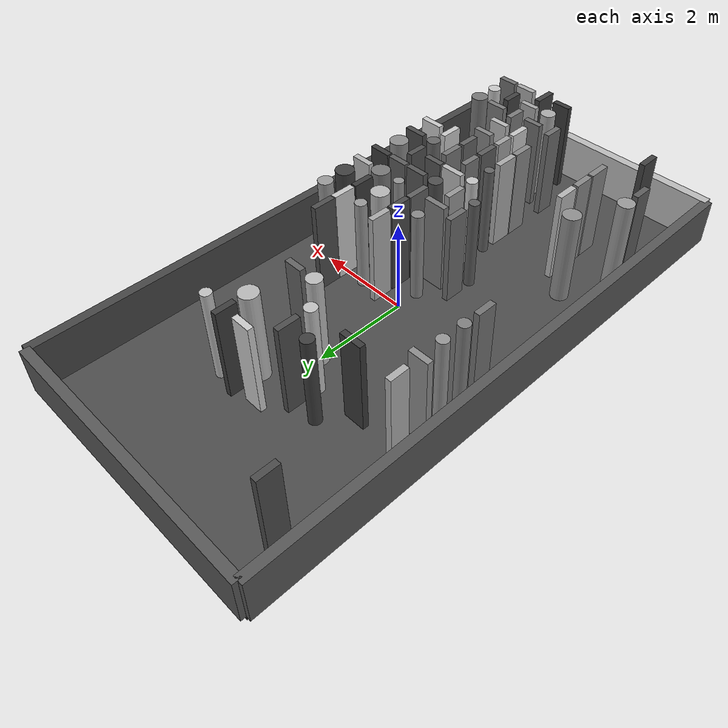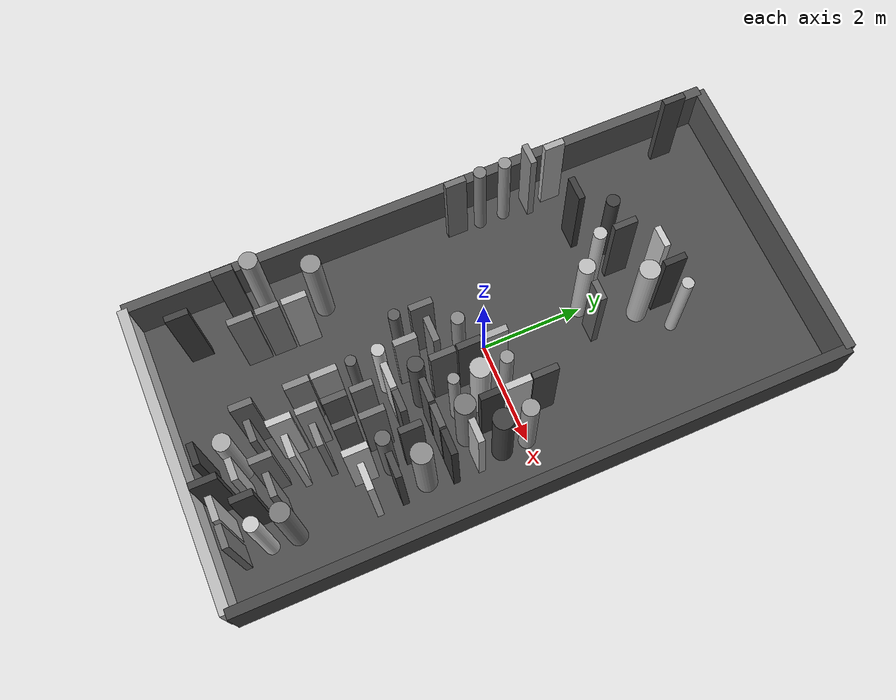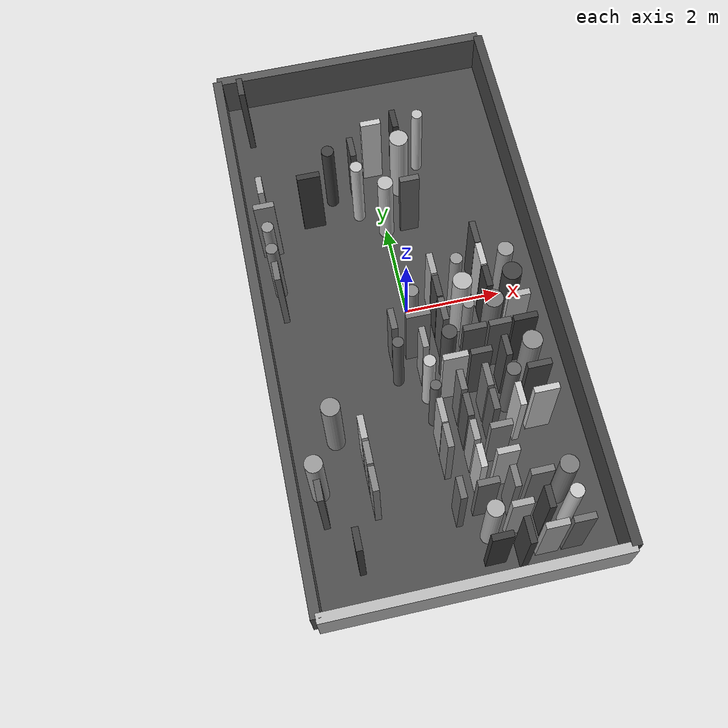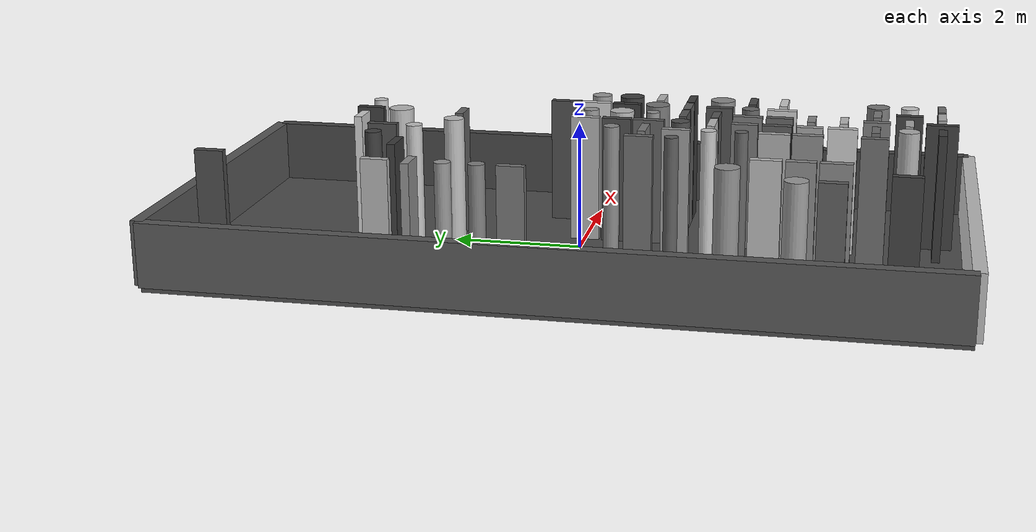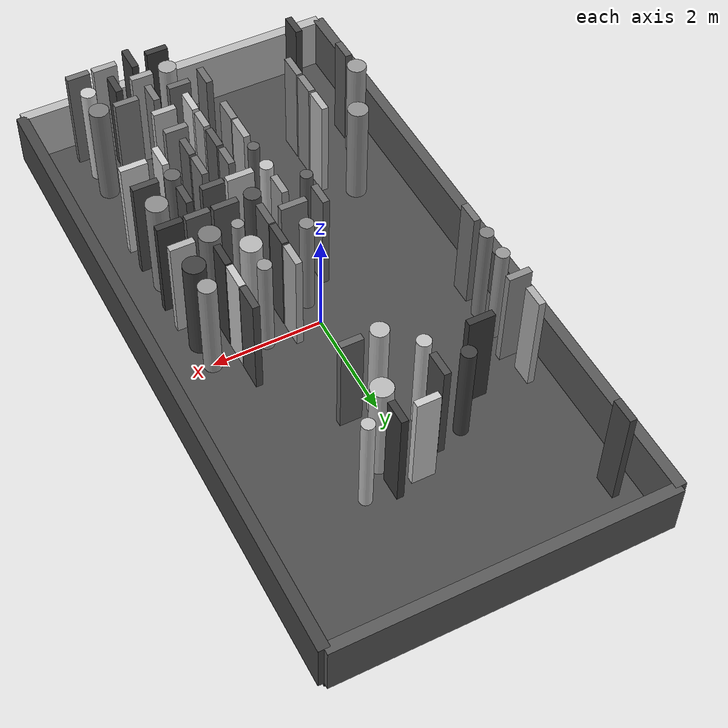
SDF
<sdf version="1.7">
  <world name="default">
    <plugin filename="gz-sim-physics-system" name="gz::sim::systems::Physics" />
    <plugin filename="gz-sim-user-commands-system" name="gz::sim::systems::UserCommands" />
    <plugin filename="gz-sim-scene-broadcaster-system" name="gz::sim::systems::SceneBroadcaster" />
    <plugin filename="gz-sim-sensors-system" name="gz::sim::systems::Sensors">
      <render_engine>ogre2</render_engine>
    </plugin>
    <plugin filename="gz-sim-imu-system" name="gz::sim::systems::Imu" />
    <plugin filename="gz-sim-contact-system" name="gz::sim::systems::Contact" />
    <light name="sun" type="directional">
      <cast_shadows>true</cast_shadows>
      <direction>-0.5 -0.5 -1</direction>
      <diffuse>1 1 1 1</diffuse>
      <specular>0.1 0.1 0.1 1</specular>
      <intensity>1.0</intensity>
    </light>
    <physics type="ode">
      <max_step_size>0.001</max_step_size>
      <real_time_factor>1.0</real_time_factor>
      <ode>
        <solver>
          <type>quick</type>
          <iters>150</iters>
          <precon_iters>0</precon_iters>
          <sor>1.4</sor>
          <use_dynamic_moi_rescaling>1</use_dynamic_moi_rescaling>
        </solver>
        <constraints>
          <cfm>0.00001</cfm>
          <erp>0.2</erp>
          <contact_max_correcting_vel>2000.0</contact_max_correcting_vel>
          <contact_surface_layer>0.01</contact_surface_layer>
        </constraints>
      </ode>
    </physics>
    <model name="ground_plane">
      <static>true</static>
      <link name="link">
        <pose>0.0 0.0 -0.05 0 0 0</pose>
        <visual name="visual">
          <material>
            <ambient>0.3007133506330439 0.3007133506330439 0.3007133506330439 1</ambient>
            <diffuse>0.3007133506330439 0.3007133506330439 0.3007133506330439 1</diffuse>
          </material>
          <geometry>
            <box>
              <size>6.0 12.0 0.1</size>
            </box>
          </geometry>
        </visual>
        <collision name="collision">
          <geometry>
            <box>
              <size>6.0 12.0 0.1</size>
            </box>
          </geometry>
          <surface>
            <friction>
              <ode>
                <mu>100</mu>
                <mu2>50.0</mu2>
                <slip1>0.0</slip1>
                <slip2>0.0</slip2>
              </ode>
            </friction>
            <bounce />
            <contact>
              <ode>
                <kp>10000.0</kp>
                <kd>100.0</kd>
              </ode>
            </contact>
          </surface>
        </collision>
      </link>
    </model>
    <model name="pn_wall_0">
      <static>true</static>
      <link name="link">
        <pose>-2.5 -4.0 1.0 0 0 0</pose>
        <visual name="visual">
          <material>
            <ambient>0.3650175910214716 0.3650175910214716 0.3650175910214716 1</ambient>
            <diffuse>0.3650175910214716 0.3650175910214716 0.3650175910214716 1</diffuse>
          </material>
          <geometry>
            <box>
              <size>0.125 0.4025010755222667 2.0</size>
            </box>
          </geometry>
        </visual>
        <collision name="collision">
          <geometry>
            <box>
              <size>0.125 0.4025010755222667 2.0</size>
            </box>
          </geometry>
          <surface>
            <friction>
              <ode>
                <mu>100</mu>
                <mu2>50.0</mu2>
                <slip1>0.0</slip1>
                <slip2>0.0</slip2>
              </ode>
            </friction>
            <bounce />
            <contact>
              <ode>
                <kp>10000.0</kp>
                <kd>100.0</kd>
              </ode>
            </contact>
          </surface>
        </collision>
      </link>
    </model>
    <model name="pn_pillar_1">
      <static>true</static>
      <link name="link">
        <pose>-2.5 -3.5 1.0 0 0 0</pose>
        <visual name="visual">
          <material>
            <ambient>0.6060196924537469 0.6060196924537469 0.6060196924537469 1</ambient>
            <diffuse>0.6060196924537469 0.6060196924537469 0.6060196924537469 1</diffuse>
          </material>
          <geometry>
            <cylinder>
              <radius>0.17364712141640126</radius>
              <length>2.0</length>
            </cylinder>
          </geometry>
        </visual>
        <collision name="collision">
          <geometry>
            <cylinder>
              <radius>0.17364712141640126</radius>
              <length>2.0</length>
            </cylinder>
          </geometry>
          <surface>
            <friction>
              <ode>
                <mu>100</mu>
                <mu2>50.0</mu2>
                <slip1>0.0</slip1>
                <slip2>0.0</slip2>
              </ode>
            </friction>
            <bounce />
            <contact>
              <ode>
                <kp>10000.0</kp>
                <kd>100.0</kd>
              </ode>
            </contact>
          </surface>
        </collision>
      </link>
    </model>
    <model name="pn_wall_2">
      <static>true</static>
      <link name="link">
        <pose>-2.5 0.5 1.0 0 0 0</pose>
        <visual name="visual">
          <material>
            <ambient>0.4531530918111623 0.4531530918111623 0.4531530918111623 1</ambient>
            <diffuse>0.4531530918111623 0.4531530918111623 0.4531530918111623 1</diffuse>
          </material>
          <geometry>
            <box>
              <size>0.125 0.40869388326294165 2.0</size>
            </box>
          </geometry>
        </visual>
        <collision name="collision">
          <geometry>
            <box>
              <size>0.125 0.40869388326294165 2.0</size>
            </box>
          </geometry>
          <surface>
            <friction>
              <ode>
                <mu>100</mu>
                <mu2>50.0</mu2>
                <slip1>0.0</slip1>
                <slip2>0.0</slip2>
              </ode>
            </friction>
            <bounce />
            <contact>
              <ode>
                <kp>10000.0</kp>
                <kd>100.0</kd>
              </ode>
            </contact>
          </surface>
        </collision>
      </link>
    </model>
    <model name="pn_pillar_3">
      <static>true</static>
      <link name="link">
        <pose>-2.5 1.0 1.0 0 0 0</pose>
        <visual name="visual">
          <material>
            <ambient>0.5032131728620175 0.5032131728620175 0.5032131728620175 1</ambient>
            <diffuse>0.5032131728620175 0.5032131728620175 0.5032131728620175 1</diffuse>
          </material>
          <geometry>
            <cylinder>
              <radius>0.12186379748036034</radius>
              <length>2.0</length>
            </cylinder>
          </geometry>
        </visual>
        <collision name="collision">
          <geometry>
            <cylinder>
              <radius>0.12186379748036034</radius>
              <length>2.0</length>
            </cylinder>
          </geometry>
          <surface>
            <friction>
              <ode>
                <mu>100</mu>
                <mu2>50.0</mu2>
                <slip1>0.0</slip1>
                <slip2>0.0</slip2>
              </ode>
            </friction>
            <bounce />
            <contact>
              <ode>
                <kp>10000.0</kp>
                <kd>100.0</kd>
              </ode>
            </contact>
          </surface>
        </collision>
      </link>
    </model>
    <model name="pn_pillar_4">
      <static>true</static>
      <link name="link">
        <pose>-2.5 1.5 1.0 0 0 0</pose>
        <visual name="visual">
          <material>
            <ambient>0.589930662667714 0.589930662667714 0.589930662667714 1</ambient>
            <diffuse>0.589930662667714 0.589930662667714 0.589930662667714 1</diffuse>
          </material>
          <geometry>
            <cylinder>
              <radius>0.11988376506866485</radius>
              <length>2.0</length>
            </cylinder>
          </geometry>
        </visual>
        <collision name="collision">
          <geometry>
            <cylinder>
              <radius>0.11988376506866485</radius>
              <length>2.0</length>
            </cylinder>
          </geometry>
          <surface>
            <friction>
              <ode>
                <mu>100</mu>
                <mu2>50.0</mu2>
                <slip1>0.0</slip1>
                <slip2>0.0</slip2>
              </ode>
            </friction>
            <bounce />
            <contact>
              <ode>
                <kp>10000.0</kp>
                <kd>100.0</kd>
              </ode>
            </contact>
          </surface>
        </collision>
      </link>
    </model>
    <model name="pn_wall_5">
      <static>true</static>
      <link name="link">
        <pose>-2.5 2.0 1.0 0 0 0</pose>
        <visual name="visual">
          <material>
            <ambient>0.5535594103255452 0.5535594103255452 0.5535594103255452 1</ambient>
            <diffuse>0.5535594103255452 0.5535594103255452 0.5535594103255452 1</diffuse>
          </material>
          <geometry>
            <box>
              <size>0.4220440622040697 0.125 2.0</size>
            </box>
          </geometry>
        </visual>
        <collision name="collision">
          <geometry>
            <box>
              <size>0.4220440622040697 0.125 2.0</size>
            </box>
          </geometry>
          <surface>
            <friction>
              <ode>
                <mu>100</mu>
                <mu2>50.0</mu2>
                <slip1>0.0</slip1>
                <slip2>0.0</slip2>
              </ode>
            </friction>
            <bounce />
            <contact>
              <ode>
                <kp>10000.0</kp>
                <kd>100.0</kd>
              </ode>
            </contact>
          </surface>
        </collision>
      </link>
    </model>
    <model name="pn_wall_6">
      <static>true</static>
      <link name="link">
        <pose>-2.5 2.5 1.0 0 0 0</pose>
        <visual name="visual">
          <material>
            <ambient>0.6834915510996848 0.6834915510996848 0.6834915510996848 1</ambient>
            <diffuse>0.6834915510996848 0.6834915510996848 0.6834915510996848 1</diffuse>
          </material>
          <geometry>
            <box>
              <size>0.125 0.4006498759678061 2.0</size>
            </box>
          </geometry>
        </visual>
        <collision name="collision">
          <geometry>
            <box>
              <size>0.125 0.4006498759678061 2.0</size>
            </box>
          </geometry>
          <surface>
            <friction>
              <ode>
                <mu>100</mu>
                <mu2>50.0</mu2>
                <slip1>0.0</slip1>
                <slip2>0.0</slip2>
              </ode>
            </friction>
            <bounce />
            <contact>
              <ode>
                <kp>10000.0</kp>
                <kd>100.0</kd>
              </ode>
            </contact>
          </surface>
        </collision>
      </link>
    </model>
    <model name="pn_wall_7">
      <static>true</static>
      <link name="link">
        <pose>-2.5 5.0 1.0 0 0 0</pose>
        <visual name="visual">
          <material>
            <ambient>0.29328769988706893 0.29328769988706893 0.29328769988706893 1</ambient>
            <diffuse>0.29328769988706893 0.29328769988706893 0.29328769988706893 1</diffuse>
          </material>
          <geometry>
            <box>
              <size>0.125 0.4340250516517992 2.0</size>
            </box>
          </geometry>
        </visual>
        <collision name="collision">
          <geometry>
            <box>
              <size>0.125 0.4340250516517992 2.0</size>
            </box>
          </geometry>
          <surface>
            <friction>
              <ode>
                <mu>100</mu>
                <mu2>50.0</mu2>
                <slip1>0.0</slip1>
                <slip2>0.0</slip2>
              </ode>
            </friction>
            <bounce />
            <contact>
              <ode>
                <kp>10000.0</kp>
                <kd>100.0</kd>
              </ode>
            </contact>
          </surface>
        </collision>
      </link>
    </model>
    <model name="pn_wall_8">
      <static>true</static>
      <link name="link">
        <pose>-2.0 -5.0 1.0 0 0 0</pose>
        <visual name="visual">
          <material>
            <ambient>0.2556475060280888 0.2556475060280888 0.2556475060280888 1</ambient>
            <diffuse>0.2556475060280888 0.2556475060280888 0.2556475060280888 1</diffuse>
          </material>
          <geometry>
            <box>
              <size>0.125 0.4336594545112627 2.0</size>
            </box>
          </geometry>
        </visual>
        <collision name="collision">
          <geometry>
            <box>
              <size>0.125 0.4336594545112627 2.0</size>
            </box>
          </geometry>
          <surface>
            <friction>
              <ode>
                <mu>100</mu>
                <mu2>50.0</mu2>
                <slip1>0.0</slip1>
                <slip2>0.0</slip2>
              </ode>
            </friction>
            <bounce />
            <contact>
              <ode>
                <kp>10000.0</kp>
                <kd>100.0</kd>
              </ode>
            </contact>
          </surface>
        </collision>
      </link>
    </model>
    <model name="pn_pillar_9">
      <static>true</static>
      <link name="link">
        <pose>-2.0 -2.5 1.0 0 0 0</pose>
        <visual name="visual">
          <material>
            <ambient>0.5622356188201347 0.5622356188201347 0.5622356188201347 1</ambient>
            <diffuse>0.5622356188201347 0.5622356188201347 0.5622356188201347 1</diffuse>
          </material>
          <geometry>
            <cylinder>
              <radius>0.184749436634746</radius>
              <length>2.0</length>
            </cylinder>
          </geometry>
        </visual>
        <collision name="collision">
          <geometry>
            <cylinder>
              <radius>0.184749436634746</radius>
              <length>2.0</length>
            </cylinder>
          </geometry>
          <surface>
            <friction>
              <ode>
                <mu>100</mu>
                <mu2>50.0</mu2>
                <slip1>0.0</slip1>
                <slip2>0.0</slip2>
              </ode>
            </friction>
            <bounce />
            <contact>
              <ode>
                <kp>10000.0</kp>
                <kd>100.0</kd>
              </ode>
            </contact>
          </surface>
        </collision>
      </link>
    </model>
    <model name="pn_wall_10">
      <static>true</static>
      <link name="link">
        <pose>-1.5 -4.0 1.0 0 0 0</pose>
        <visual name="visual">
          <material>
            <ambient>0.5217368548728205 0.5217368548728205 0.5217368548728205 1</ambient>
            <diffuse>0.5217368548728205 0.5217368548728205 0.5217368548728205 1</diffuse>
          </material>
          <geometry>
            <box>
              <size>0.125 0.4729731786693818 2.0</size>
            </box>
          </geometry>
        </visual>
        <collision name="collision">
          <geometry>
            <box>
              <size>0.125 0.4729731786693818 2.0</size>
            </box>
          </geometry>
          <surface>
            <friction>
              <ode>
                <mu>100</mu>
                <mu2>50.0</mu2>
                <slip1>0.0</slip1>
                <slip2>0.0</slip2>
              </ode>
            </friction>
            <bounce />
            <contact>
              <ode>
                <kp>10000.0</kp>
                <kd>100.0</kd>
              </ode>
            </contact>
          </surface>
        </collision>
      </link>
    </model>
    <model name="pn_wall_11">
      <static>true</static>
      <link name="link">
        <pose>-1.5 -3.5 1.0 0 0 0</pose>
        <visual name="visual">
          <material>
            <ambient>0.5312243787639362 0.5312243787639362 0.5312243787639362 1</ambient>
            <diffuse>0.5312243787639362 0.5312243787639362 0.5312243787639362 1</diffuse>
          </material>
          <geometry>
            <box>
              <size>0.125 0.43785343772083535 2.0</size>
            </box>
          </geometry>
        </visual>
        <collision name="collision">
          <geometry>
            <box>
              <size>0.125 0.43785343772083535 2.0</size>
            </box>
          </geometry>
          <surface>
            <friction>
              <ode>
                <mu>100</mu>
                <mu2>50.0</mu2>
                <slip1>0.0</slip1>
                <slip2>0.0</slip2>
              </ode>
            </friction>
            <bounce />
            <contact>
              <ode>
                <kp>10000.0</kp>
                <kd>100.0</kd>
              </ode>
            </contact>
          </surface>
        </collision>
      </link>
    </model>
    <model name="pn_wall_12">
      <static>true</static>
      <link name="link">
        <pose>-1.5 -3.0 1.0 0 0 0</pose>
        <visual name="visual">
          <material>
            <ambient>0.7170241401864663 0.7170241401864663 0.7170241401864663 1</ambient>
            <diffuse>0.7170241401864663 0.7170241401864663 0.7170241401864663 1</diffuse>
          </material>
          <geometry>
            <box>
              <size>0.125 0.46185197523642463 2.0</size>
            </box>
          </geometry>
        </visual>
        <collision name="collision">
          <geometry>
            <box>
              <size>0.125 0.46185197523642463 2.0</size>
            </box>
          </geometry>
          <surface>
            <friction>
              <ode>
                <mu>100</mu>
                <mu2>50.0</mu2>
                <slip1>0.0</slip1>
                <slip2>0.0</slip2>
              </ode>
            </friction>
            <bounce />
            <contact>
              <ode>
                <kp>10000.0</kp>
                <kd>100.0</kd>
              </ode>
            </contact>
          </surface>
        </collision>
      </link>
    </model>
    <model name="pn_wall_13">
      <static>true</static>
      <link name="link">
        <pose>-1.5 2.5 1.0 0 0 0</pose>
        <visual name="visual">
          <material>
            <ambient>0.22749463019339733 0.22749463019339733 0.22749463019339733 1</ambient>
            <diffuse>0.22749463019339733 0.22749463019339733 0.22749463019339733 1</diffuse>
          </material>
          <geometry>
            <box>
              <size>0.47045718362149236 0.125 2.0</size>
            </box>
          </geometry>
        </visual>
        <collision name="collision">
          <geometry>
            <box>
              <size>0.47045718362149236 0.125 2.0</size>
            </box>
          </geometry>
          <surface>
            <friction>
              <ode>
                <mu>100</mu>
                <mu2>50.0</mu2>
                <slip1>0.0</slip1>
                <slip2>0.0</slip2>
              </ode>
            </friction>
            <bounce />
            <contact>
              <ode>
                <kp>10000.0</kp>
                <kd>100.0</kd>
              </ode>
            </contact>
          </surface>
        </collision>
      </link>
    </model>
    <model name="pn_pillar_14">
      <static>true</static>
      <link name="link">
        <pose>-1.0 3.0 1.0 0 0 0</pose>
        <visual name="visual">
          <material>
            <ambient>0.24787518615417653 0.24787518615417653 0.24787518615417653 1</ambient>
            <diffuse>0.24787518615417653 0.24787518615417653 0.24787518615417653 1</diffuse>
          </material>
          <geometry>
            <cylinder>
              <radius>0.12893879636021072</radius>
              <length>2.0</length>
            </cylinder>
          </geometry>
        </visual>
        <collision name="collision">
          <geometry>
            <cylinder>
              <radius>0.12893879636021072</radius>
              <length>2.0</length>
            </cylinder>
          </geometry>
          <surface>
            <friction>
              <ode>
                <mu>100</mu>
                <mu2>50.0</mu2>
                <slip1>0.0</slip1>
                <slip2>0.0</slip2>
              </ode>
            </friction>
            <bounce />
            <contact>
              <ode>
                <kp>10000.0</kp>
                <kd>100.0</kd>
              </ode>
            </contact>
          </surface>
        </collision>
      </link>
    </model>
    <model name="pn_pillar_15">
      <static>true</static>
      <link name="link">
        <pose>-0.5 -1.5 1.0 0 0 0</pose>
        <visual name="visual">
          <material>
            <ambient>0.36678416186605534 0.36678416186605534 0.36678416186605534 1</ambient>
            <diffuse>0.36678416186605534 0.36678416186605534 0.36678416186605534 1</diffuse>
          </material>
          <geometry>
            <cylinder>
              <radius>0.11010014294097292</radius>
              <length>2.0</length>
            </cylinder>
          </geometry>
        </visual>
        <collision name="collision">
          <geometry>
            <cylinder>
              <radius>0.11010014294097292</radius>
              <length>2.0</length>
            </cylinder>
          </geometry>
          <surface>
            <friction>
              <ode>
                <mu>100</mu>
                <mu2>50.0</mu2>
                <slip1>0.0</slip1>
                <slip2>0.0</slip2>
              </ode>
            </friction>
            <bounce />
            <contact>
              <ode>
                <kp>10000.0</kp>
                <kd>100.0</kd>
              </ode>
            </contact>
          </surface>
        </collision>
      </link>
    </model>
    <model name="pn_wall_16">
      <static>true</static>
      <link name="link">
        <pose>-0.5 -1.0 1.0 0 0 0</pose>
        <visual name="visual">
          <material>
            <ambient>0.42210858027012965 0.42210858027012965 0.42210858027012965 1</ambient>
            <diffuse>0.42210858027012965 0.42210858027012965 0.42210858027012965 1</diffuse>
          </material>
          <geometry>
            <box>
              <size>0.125 0.43648321789700845 2.0</size>
            </box>
          </geometry>
        </visual>
        <collision name="collision">
          <geometry>
            <box>
              <size>0.125 0.43648321789700845 2.0</size>
            </box>
          </geometry>
          <surface>
            <friction>
              <ode>
                <mu>100</mu>
                <mu2>50.0</mu2>
                <slip1>0.0</slip1>
                <slip2>0.0</slip2>
              </ode>
            </friction>
            <bounce />
            <contact>
              <ode>
                <kp>10000.0</kp>
                <kd>100.0</kd>
              </ode>
            </contact>
          </surface>
        </collision>
      </link>
    </model>
    <model name="pn_pillar_17">
      <static>true</static>
      <link name="link">
        <pose>-0.5 2.5 1.0 0 0 0</pose>
        <visual name="visual">
          <material>
            <ambient>0.7619927526274966 0.7619927526274966 0.7619927526274966 1</ambient>
            <diffuse>0.7619927526274966 0.7619927526274966 0.7619927526274966 1</diffuse>
          </material>
          <geometry>
            <cylinder>
              <radius>0.12669778220491135</radius>
              <length>2.0</length>
            </cylinder>
          </geometry>
        </visual>
        <collision name="collision">
          <geometry>
            <cylinder>
              <radius>0.12669778220491135</radius>
              <length>2.0</length>
            </cylinder>
          </geometry>
          <surface>
            <friction>
              <ode>
                <mu>100</mu>
                <mu2>50.0</mu2>
                <slip1>0.0</slip1>
                <slip2>0.0</slip2>
              </ode>
            </friction>
            <bounce />
            <contact>
              <ode>
                <kp>10000.0</kp>
                <kd>100.0</kd>
              </ode>
            </contact>
          </surface>
        </collision>
      </link>
    </model>
    <model name="pn_wall_18">
      <static>true</static>
      <link name="link">
        <pose>-0.5 3.0 1.0 0 0 0</pose>
        <visual name="visual">
          <material>
            <ambient>0.3026831889188582 0.3026831889188582 0.3026831889188582 1</ambient>
            <diffuse>0.3026831889188582 0.3026831889188582 0.3026831889188582 1</diffuse>
          </material>
          <geometry>
            <box>
              <size>0.125 0.4609131005666988 2.0</size>
            </box>
          </geometry>
        </visual>
        <collision name="collision">
          <geometry>
            <box>
              <size>0.125 0.4609131005666988 2.0</size>
            </box>
          </geometry>
          <surface>
            <friction>
              <ode>
                <mu>100</mu>
                <mu2>50.0</mu2>
                <slip1>0.0</slip1>
                <slip2>0.0</slip2>
              </ode>
            </friction>
            <bounce />
            <contact>
              <ode>
                <kp>10000.0</kp>
                <kd>100.0</kd>
              </ode>
            </contact>
          </surface>
        </collision>
      </link>
    </model>
    <model name="pn_wall_19">
      <static>true</static>
      <link name="link">
        <pose>0.0 -4.5 1.0 0 0 0</pose>
        <visual name="visual">
          <material>
            <ambient>0.4276732650545887 0.4276732650545887 0.4276732650545887 1</ambient>
            <diffuse>0.4276732650545887 0.4276732650545887 0.4276732650545887 1</diffuse>
          </material>
          <geometry>
            <box>
              <size>0.125 0.41634024937619285 2.0</size>
            </box>
          </geometry>
        </visual>
        <collision name="collision">
          <geometry>
            <box>
              <size>0.125 0.41634024937619285 2.0</size>
            </box>
          </geometry>
          <surface>
            <friction>
              <ode>
                <mu>100</mu>
                <mu2>50.0</mu2>
                <slip1>0.0</slip1>
                <slip2>0.0</slip2>
              </ode>
            </friction>
            <bounce />
            <contact>
              <ode>
                <kp>10000.0</kp>
                <kd>100.0</kd>
              </ode>
            </contact>
          </surface>
        </collision>
      </link>
    </model>
    <model name="pn_wall_20">
      <static>true</static>
      <link name="link">
        <pose>0.0 -3.5 1.0 0 0 0</pose>
        <visual name="visual">
          <material>
            <ambient>0.5341698462647878 0.5341698462647878 0.5341698462647878 1</ambient>
            <diffuse>0.5341698462647878 0.5341698462647878 0.5341698462647878 1</diffuse>
          </material>
          <geometry>
            <box>
              <size>0.125 0.4639999759854093 2.0</size>
            </box>
          </geometry>
        </visual>
        <collision name="collision">
          <geometry>
            <box>
              <size>0.125 0.4639999759854093 2.0</size>
            </box>
          </geometry>
          <surface>
            <friction>
              <ode>
                <mu>100</mu>
                <mu2>50.0</mu2>
                <slip1>0.0</slip1>
                <slip2>0.0</slip2>
              </ode>
            </friction>
            <bounce />
            <contact>
              <ode>
                <kp>10000.0</kp>
                <kd>100.0</kd>
              </ode>
            </contact>
          </surface>
        </collision>
      </link>
    </model>
    <model name="pn_wall_21">
      <static>true</static>
      <link name="link">
        <pose>0.0 -3.0 1.0 0 0 0</pose>
        <visual name="visual">
          <material>
            <ambient>0.6655999469277469 0.6655999469277469 0.6655999469277469 1</ambient>
            <diffuse>0.6655999469277469 0.6655999469277469 0.6655999469277469 1</diffuse>
          </material>
          <geometry>
            <box>
              <size>0.125 0.48428519201898096 2.0</size>
            </box>
          </geometry>
        </visual>
        <collision name="collision">
          <geometry>
            <box>
              <size>0.125 0.48428519201898096 2.0</size>
            </box>
          </geometry>
          <surface>
            <friction>
              <ode>
                <mu>100</mu>
                <mu2>50.0</mu2>
                <slip1>0.0</slip1>
                <slip2>0.0</slip2>
              </ode>
            </friction>
            <bounce />
            <contact>
              <ode>
                <kp>10000.0</kp>
                <kd>100.0</kd>
              </ode>
            </contact>
          </surface>
        </collision>
      </link>
    </model>
    <model name="pn_pillar_22">
      <static>true</static>
      <link name="link">
        <pose>0.0 -2.5 1.0 0 0 0</pose>
        <visual name="visual">
          <material>
            <ambient>0.3892718288354492 0.3892718288354492 0.3892718288354492 1</ambient>
            <diffuse>0.3892718288354492 0.3892718288354492 0.3892718288354492 1</diffuse>
          </material>
          <geometry>
            <cylinder>
              <radius>0.10321002439040378</radius>
              <length>2.0</length>
            </cylinder>
          </geometry>
        </visual>
        <collision name="collision">
          <geometry>
            <cylinder>
              <radius>0.10321002439040378</radius>
              <length>2.0</length>
            </cylinder>
          </geometry>
          <surface>
            <friction>
              <ode>
                <mu>100</mu>
                <mu2>50.0</mu2>
                <slip1>0.0</slip1>
                <slip2>0.0</slip2>
              </ode>
            </friction>
            <bounce />
            <contact>
              <ode>
                <kp>10000.0</kp>
                <kd>100.0</kd>
              </ode>
            </contact>
          </surface>
        </collision>
      </link>
    </model>
    <model name="pn_pillar_23">
      <static>true</static>
      <link name="link">
        <pose>0.0 -2.0 1.0 0 0 0</pose>
        <visual name="visual">
          <material>
            <ambient>0.7657458286010328 0.7657458286010328 0.7657458286010328 1</ambient>
            <diffuse>0.7657458286010328 0.7657458286010328 0.7657458286010328 1</diffuse>
          </material>
          <geometry>
            <cylinder>
              <radius>0.12109828435863265</radius>
              <length>2.0</length>
            </cylinder>
          </geometry>
        </visual>
        <collision name="collision">
          <geometry>
            <cylinder>
              <radius>0.12109828435863265</radius>
              <length>2.0</length>
            </cylinder>
          </geometry>
          <surface>
            <friction>
              <ode>
                <mu>100</mu>
                <mu2>50.0</mu2>
                <slip1>0.0</slip1>
                <slip2>0.0</slip2>
              </ode>
            </friction>
            <bounce />
            <contact>
              <ode>
                <kp>10000.0</kp>
                <kd>100.0</kd>
              </ode>
            </contact>
          </surface>
        </collision>
      </link>
    </model>
    <model name="pn_wall_24">
      <static>true</static>
      <link name="link">
        <pose>0.0 -1.5 1.0 0 0 0</pose>
        <visual name="visual">
          <material>
            <ambient>0.5932631991769282 0.5932631991769282 0.5932631991769282 1</ambient>
            <diffuse>0.5932631991769282 0.5932631991769282 0.5932631991769282 1</diffuse>
          </material>
          <geometry>
            <box>
              <size>0.125 0.4314677880798478 2.0</size>
            </box>
          </geometry>
        </visual>
        <collision name="collision">
          <geometry>
            <box>
              <size>0.125 0.4314677880798478 2.0</size>
            </box>
          </geometry>
          <surface>
            <friction>
              <ode>
                <mu>100</mu>
                <mu2>50.0</mu2>
                <slip1>0.0</slip1>
                <slip2>0.0</slip2>
              </ode>
            </friction>
            <bounce />
            <contact>
              <ode>
                <kp>10000.0</kp>
                <kd>100.0</kd>
              </ode>
            </contact>
          </surface>
        </collision>
      </link>
    </model>
    <model name="pn_wall_25">
      <static>true</static>
      <link name="link">
        <pose>0.0 -1.0 1.0 0 0 0</pose>
        <visual name="visual">
          <material>
            <ambient>0.4753111115524393 0.4753111115524393 0.4753111115524393 1</ambient>
            <diffuse>0.4753111115524393 0.4753111115524393 0.4753111115524393 1</diffuse>
          </material>
          <geometry>
            <box>
              <size>0.49145475897405433 0.125 2.0</size>
            </box>
          </geometry>
        </visual>
        <collision name="collision">
          <geometry>
            <box>
              <size>0.49145475897405433 0.125 2.0</size>
            </box>
          </geometry>
          <surface>
            <friction>
              <ode>
                <mu>100</mu>
                <mu2>50.0</mu2>
                <slip1>0.0</slip1>
                <slip2>0.0</slip2>
              </ode>
            </friction>
            <bounce />
            <contact>
              <ode>
                <kp>10000.0</kp>
                <kd>100.0</kd>
              </ode>
            </contact>
          </surface>
        </collision>
      </link>
    </model>
    <model name="pn_pillar_26">
      <static>true</static>
      <link name="link">
        <pose>0.0 -0.5 1.0 0 0 0</pose>
        <visual name="visual">
          <material>
            <ambient>0.5368208804978905 0.5368208804978905 0.5368208804978905 1</ambient>
            <diffuse>0.5368208804978905 0.5368208804978905 0.5368208804978905 1</diffuse>
          </material>
          <geometry>
            <cylinder>
              <radius>0.12466275076939835</radius>
              <length>2.0</length>
            </cylinder>
          </geometry>
        </visual>
        <collision name="collision">
          <geometry>
            <cylinder>
              <radius>0.12466275076939835</radius>
              <length>2.0</length>
            </cylinder>
          </geometry>
          <surface>
            <friction>
              <ode>
                <mu>100</mu>
                <mu2>50.0</mu2>
                <slip1>0.0</slip1>
                <slip2>0.0</slip2>
              </ode>
            </friction>
            <bounce />
            <contact>
              <ode>
                <kp>10000.0</kp>
                <kd>100.0</kd>
              </ode>
            </contact>
          </surface>
        </collision>
      </link>
    </model>
    <model name="pn_pillar_27">
      <static>true</static>
      <link name="link">
        <pose>0.0 2.0 1.0 0 0 0</pose>
        <visual name="visual">
          <material>
            <ambient>0.7386937301614862 0.7386937301614862 0.7386937301614862 1</ambient>
            <diffuse>0.7386937301614862 0.7386937301614862 0.7386937301614862 1</diffuse>
          </material>
          <geometry>
            <cylinder>
              <radius>0.15845859902235407</radius>
              <length>2.0</length>
            </cylinder>
          </geometry>
        </visual>
        <collision name="collision">
          <geometry>
            <cylinder>
              <radius>0.15845859902235407</radius>
              <length>2.0</length>
            </cylinder>
          </geometry>
          <surface>
            <friction>
              <ode>
                <mu>100</mu>
                <mu2>50.0</mu2>
                <slip1>0.0</slip1>
                <slip2>0.0</slip2>
              </ode>
            </friction>
            <bounce />
            <contact>
              <ode>
                <kp>10000.0</kp>
                <kd>100.0</kd>
              </ode>
            </contact>
          </surface>
        </collision>
      </link>
    </model>
    <model name="pn_wall_28">
      <static>true</static>
      <link name="link">
        <pose>0.0 3.5 1.0 0 0 0</pose>
        <visual name="visual">
          <material>
            <ambient>0.7985225638970663 0.7985225638970663 0.7985225638970663 1</ambient>
            <diffuse>0.7985225638970663 0.7985225638970663 0.7985225638970663 1</diffuse>
          </material>
          <geometry>
            <box>
              <size>0.42193207591572834 0.125 2.0</size>
            </box>
          </geometry>
        </visual>
        <collision name="collision">
          <geometry>
            <box>
              <size>0.42193207591572834 0.125 2.0</size>
            </box>
          </geometry>
          <surface>
            <friction>
              <ode>
                <mu>100</mu>
                <mu2>50.0</mu2>
                <slip1>0.0</slip1>
                <slip2>0.0</slip2>
              </ode>
            </friction>
            <bounce />
            <contact>
              <ode>
                <kp>10000.0</kp>
                <kd>100.0</kd>
              </ode>
            </contact>
          </surface>
        </collision>
      </link>
    </model>
    <model name="pn_wall_29">
      <static>true</static>
      <link name="link">
        <pose>0.5 -5.5 1.0 0 0 0</pose>
        <visual name="visual">
          <material>
            <ambient>0.22826982525484074 0.22826982525484074 0.22826982525484074 1</ambient>
            <diffuse>0.22826982525484074 0.22826982525484074 0.22826982525484074 1</diffuse>
          </material>
          <geometry>
            <box>
              <size>0.40909094121737943 0.125 2.0</size>
            </box>
          </geometry>
        </visual>
        <collision name="collision">
          <geometry>
            <box>
              <size>0.40909094121737943 0.125 2.0</size>
            </box>
          </geometry>
          <surface>
            <friction>
              <ode>
                <mu>100</mu>
                <mu2>50.0</mu2>
                <slip1>0.0</slip1>
                <slip2>0.0</slip2>
              </ode>
            </friction>
            <bounce />
            <contact>
              <ode>
                <kp>10000.0</kp>
                <kd>100.0</kd>
              </ode>
            </contact>
          </surface>
        </collision>
      </link>
    </model>
    <model name="pn_pillar_30">
      <static>true</static>
      <link name="link">
        <pose>0.5 -5.0 1.0 0 0 0</pose>
        <visual name="visual">
          <material>
            <ambient>0.6752476186177785 0.6752476186177785 0.6752476186177785 1</ambient>
            <diffuse>0.6752476186177785 0.6752476186177785 0.6752476186177785 1</diffuse>
          </material>
          <geometry>
            <cylinder>
              <radius>0.162744604170309</radius>
              <length>2.0</length>
            </cylinder>
          </geometry>
        </visual>
        <collision name="collision">
          <geometry>
            <cylinder>
              <radius>0.162744604170309</radius>
              <length>2.0</length>
            </cylinder>
          </geometry>
          <surface>
            <friction>
              <ode>
                <mu>100</mu>
                <mu2>50.0</mu2>
                <slip1>0.0</slip1>
                <slip2>0.0</slip2>
              </ode>
            </friction>
            <bounce />
            <contact>
              <ode>
                <kp>10000.0</kp>
                <kd>100.0</kd>
              </ode>
            </contact>
          </surface>
        </collision>
      </link>
    </model>
    <model name="pn_wall_31">
      <static>true</static>
      <link name="link">
        <pose>0.5 -4.5 1.0 0 0 0</pose>
        <visual name="visual">
          <material>
            <ambient>0.4289715719039221 0.4289715719039221 0.4289715719039221 1</ambient>
            <diffuse>0.4289715719039221 0.4289715719039221 0.4289715719039221 1</diffuse>
          </material>
          <geometry>
            <box>
              <size>0.40635277061519576 0.125 2.0</size>
            </box>
          </geometry>
        </visual>
        <collision name="collision">
          <geometry>
            <box>
              <size>0.40635277061519576 0.125 2.0</size>
            </box>
          </geometry>
          <surface>
            <friction>
              <ode>
                <mu>100</mu>
                <mu2>50.0</mu2>
                <slip1>0.0</slip1>
                <slip2>0.0</slip2>
              </ode>
            </friction>
            <bounce />
            <contact>
              <ode>
                <kp>10000.0</kp>
                <kd>100.0</kd>
              </ode>
            </contact>
          </surface>
        </collision>
      </link>
    </model>
    <model name="pn_wall_32">
      <static>true</static>
      <link name="link">
        <pose>0.5 -4.0 1.0 0 0 0</pose>
        <visual name="visual">
          <material>
            <ambient>0.7826470265681711 0.7826470265681711 0.7826470265681711 1</ambient>
            <diffuse>0.7826470265681711 0.7826470265681711 0.7826470265681711 1</diffuse>
          </material>
          <geometry>
            <box>
              <size>0.125 0.4529114345099137 2.0</size>
            </box>
          </geometry>
        </visual>
        <collision name="collision">
          <geometry>
            <box>
              <size>0.125 0.4529114345099137 2.0</size>
            </box>
          </geometry>
          <surface>
            <friction>
              <ode>
                <mu>100</mu>
                <mu2>50.0</mu2>
                <slip1>0.0</slip1>
                <slip2>0.0</slip2>
              </ode>
            </friction>
            <bounce />
            <contact>
              <ode>
                <kp>10000.0</kp>
                <kd>100.0</kd>
              </ode>
            </contact>
          </surface>
        </collision>
      </link>
    </model>
    <model name="pn_wall_33">
      <static>true</static>
      <link name="link">
        <pose>0.5 -3.5 1.0 0 0 0</pose>
        <visual name="visual">
          <material>
            <ambient>0.6324330916161169 0.6324330916161169 0.6324330916161169 1</ambient>
            <diffuse>0.6324330916161169 0.6324330916161169 0.6324330916161169 1</diffuse>
          </material>
          <geometry>
            <box>
              <size>0.125 0.401148102194282 2.0</size>
            </box>
          </geometry>
        </visual>
        <collision name="collision">
          <geometry>
            <box>
              <size>0.125 0.401148102194282 2.0</size>
            </box>
          </geometry>
          <surface>
            <friction>
              <ode>
                <mu>100</mu>
                <mu2>50.0</mu2>
                <slip1>0.0</slip1>
                <slip2>0.0</slip2>
              </ode>
            </friction>
            <bounce />
            <contact>
              <ode>
                <kp>10000.0</kp>
                <kd>100.0</kd>
              </ode>
            </contact>
          </surface>
        </collision>
      </link>
    </model>
    <model name="pn_wall_34">
      <static>true</static>
      <link name="link">
        <pose>0.5 -3.0 1.0 0 0 0</pose>
        <visual name="visual">
          <material>
            <ambient>0.3600951139715257 0.3600951139715257 0.3600951139715257 1</ambient>
            <diffuse>0.3600951139715257 0.3600951139715257 0.3600951139715257 1</diffuse>
          </material>
          <geometry>
            <box>
              <size>0.125 0.45369703304087955 2.0</size>
            </box>
          </geometry>
        </visual>
        <collision name="collision">
          <geometry>
            <box>
              <size>0.125 0.45369703304087955 2.0</size>
            </box>
          </geometry>
          <surface>
            <friction>
              <ode>
                <mu>100</mu>
                <mu2>50.0</mu2>
                <slip1>0.0</slip1>
                <slip2>0.0</slip2>
              </ode>
            </friction>
            <bounce />
            <contact>
              <ode>
                <kp>10000.0</kp>
                <kd>100.0</kd>
              </ode>
            </contact>
          </surface>
        </collision>
      </link>
    </model>
    <model name="pn_wall_35">
      <static>true</static>
      <link name="link">
        <pose>0.5 -2.5 1.0 0 0 0</pose>
        <visual name="visual">
          <material>
            <ambient>0.460859150401463 0.460859150401463 0.460859150401463 1</ambient>
            <diffuse>0.460859150401463 0.460859150401463 0.460859150401463 1</diffuse>
          </material>
          <geometry>
            <box>
              <size>0.125 0.41115521735958765 2.0</size>
            </box>
          </geometry>
        </visual>
        <collision name="collision">
          <geometry>
            <box>
              <size>0.125 0.41115521735958765 2.0</size>
            </box>
          </geometry>
          <surface>
            <friction>
              <ode>
                <mu>100</mu>
                <mu2>50.0</mu2>
                <slip1>0.0</slip1>
                <slip2>0.0</slip2>
              </ode>
            </friction>
            <bounce />
            <contact>
              <ode>
                <kp>10000.0</kp>
                <kd>100.0</kd>
              </ode>
            </contact>
          </surface>
        </collision>
      </link>
    </model>
    <model name="pn_wall_36">
      <static>true</static>
      <link name="link">
        <pose>0.5 -2.0 1.0 0 0 0</pose>
        <visual name="visual">
          <material>
            <ambient>0.7255117642269164 0.7255117642269164 0.7255117642269164 1</ambient>
            <diffuse>0.7255117642269164 0.7255117642269164 0.7255117642269164 1</diffuse>
          </material>
          <geometry>
            <box>
              <size>0.495381592752108 0.125 2.0</size>
            </box>
          </geometry>
        </visual>
        <collision name="collision">
          <geometry>
            <box>
              <size>0.495381592752108 0.125 2.0</size>
            </box>
          </geometry>
          <surface>
            <friction>
              <ode>
                <mu>100</mu>
                <mu2>50.0</mu2>
                <slip1>0.0</slip1>
                <slip2>0.0</slip2>
              </ode>
            </friction>
            <bounce />
            <contact>
              <ode>
                <kp>10000.0</kp>
                <kd>100.0</kd>
              </ode>
            </contact>
          </surface>
        </collision>
      </link>
    </model>
    <model name="pn_pillar_37">
      <static>true</static>
      <link name="link">
        <pose>0.5 -1.5 1.0 0 0 0</pose>
        <visual name="visual">
          <material>
            <ambient>0.3071911283180788 0.3071911283180788 0.3071911283180788 1</ambient>
            <diffuse>0.3071911283180788 0.3071911283180788 0.3071911283180788 1</diffuse>
          </material>
          <geometry>
            <cylinder>
              <radius>0.15005861130502984</radius>
              <length>2.0</length>
            </cylinder>
          </geometry>
        </visual>
        <collision name="collision">
          <geometry>
            <cylinder>
              <radius>0.15005861130502984</radius>
              <length>2.0</length>
            </cylinder>
          </geometry>
          <surface>
            <friction>
              <ode>
                <mu>100</mu>
                <mu2>50.0</mu2>
                <slip1>0.0</slip1>
                <slip2>0.0</slip2>
              </ode>
            </friction>
            <bounce />
            <contact>
              <ode>
                <kp>10000.0</kp>
                <kd>100.0</kd>
              </ode>
            </contact>
          </surface>
        </collision>
      </link>
    </model>
    <model name="pn_wall_38">
      <static>true</static>
      <link name="link">
        <pose>0.5 -1.0 1.0 0 0 0</pose>
        <visual name="visual">
          <material>
            <ambient>0.3790668748691798 0.3790668748691798 0.3790668748691798 1</ambient>
            <diffuse>0.3790668748691798 0.3790668748691798 0.3790668748691798 1</diffuse>
          </material>
          <geometry>
            <box>
              <size>0.125 0.4870518569836767 2.0</size>
            </box>
          </geometry>
        </visual>
        <collision name="collision">
          <geometry>
            <box>
              <size>0.125 0.4870518569836767 2.0</size>
            </box>
          </geometry>
          <surface>
            <friction>
              <ode>
                <mu>100</mu>
                <mu2>50.0</mu2>
                <slip1>0.0</slip1>
                <slip2>0.0</slip2>
              </ode>
            </friction>
            <bounce />
            <contact>
              <ode>
                <kp>10000.0</kp>
                <kd>100.0</kd>
              </ode>
            </contact>
          </surface>
        </collision>
      </link>
    </model>
    <model name="pn_wall_39">
      <static>true</static>
      <link name="link">
        <pose>0.5 -0.5 1.0 0 0 0</pose>
        <visual name="visual">
          <material>
            <ambient>0.2917035611297809 0.2917035611297809 0.2917035611297809 1</ambient>
            <diffuse>0.2917035611297809 0.2917035611297809 0.2917035611297809 1</diffuse>
          </material>
          <geometry>
            <box>
              <size>0.125 0.46089702114381725 2.0</size>
            </box>
          </geometry>
        </visual>
        <collision name="collision">
          <geometry>
            <box>
              <size>0.125 0.46089702114381725 2.0</size>
            </box>
          </geometry>
          <surface>
            <friction>
              <ode>
                <mu>100</mu>
                <mu2>50.0</mu2>
                <slip1>0.0</slip1>
                <slip2>0.0</slip2>
              </ode>
            </friction>
            <bounce />
            <contact>
              <ode>
                <kp>10000.0</kp>
                <kd>100.0</kd>
              </ode>
            </contact>
          </surface>
        </collision>
      </link>
    </model>
    <model name="pn_wall_40">
      <static>true</static>
      <link name="link">
        <pose>0.5 0.0 1.0 0 0 0</pose>
        <visual name="visual">
          <material>
            <ambient>0.6671758871783351 0.6671758871783351 0.6671758871783351 1</ambient>
            <diffuse>0.6671758871783351 0.6671758871783351 0.6671758871783351 1</diffuse>
          </material>
          <geometry>
            <box>
              <size>0.125 0.4539379030119626 2.0</size>
            </box>
          </geometry>
        </visual>
        <collision name="collision">
          <geometry>
            <box>
              <size>0.125 0.4539379030119626 2.0</size>
            </box>
          </geometry>
          <surface>
            <friction>
              <ode>
                <mu>100</mu>
                <mu2>50.0</mu2>
                <slip1>0.0</slip1>
                <slip2>0.0</slip2>
              </ode>
            </friction>
            <bounce />
            <contact>
              <ode>
                <kp>10000.0</kp>
                <kd>100.0</kd>
              </ode>
            </contact>
          </surface>
        </collision>
      </link>
    </model>
    <model name="pn_wall_41">
      <static>true</static>
      <link name="link">
        <pose>0.5 2.0 1.0 0 0 0</pose>
        <visual name="visual">
          <material>
            <ambient>0.3944936342028039 0.3944936342028039 0.3944936342028039 1</ambient>
            <diffuse>0.3944936342028039 0.3944936342028039 0.3944936342028039 1</diffuse>
          </material>
          <geometry>
            <box>
              <size>0.40005718961279435 0.125 2.0</size>
            </box>
          </geometry>
        </visual>
        <collision name="collision">
          <geometry>
            <box>
              <size>0.40005718961279435 0.125 2.0</size>
            </box>
          </geometry>
          <surface>
            <friction>
              <ode>
                <mu>100</mu>
                <mu2>50.0</mu2>
                <slip1>0.0</slip1>
                <slip2>0.0</slip2>
              </ode>
            </friction>
            <bounce />
            <contact>
              <ode>
                <kp>10000.0</kp>
                <kd>100.0</kd>
              </ode>
            </contact>
          </surface>
        </collision>
      </link>
    </model>
    <model name="pn_pillar_42">
      <static>true</static>
      <link name="link">
        <pose>0.5 3.0 1.0 0 0 0</pose>
        <visual name="visual">
          <material>
            <ambient>0.7272331266939107 0.7272331266939107 0.7272331266939107 1</ambient>
            <diffuse>0.7272331266939107 0.7272331266939107 0.7272331266939107 1</diffuse>
          </material>
          <geometry>
            <cylinder>
              <radius>0.19290986162646173</radius>
              <length>2.0</length>
            </cylinder>
          </geometry>
        </visual>
        <collision name="collision">
          <geometry>
            <cylinder>
              <radius>0.19290986162646173</radius>
              <length>2.0</length>
            </cylinder>
          </geometry>
          <surface>
            <friction>
              <ode>
                <mu>100</mu>
                <mu2>50.0</mu2>
                <slip1>0.0</slip1>
                <slip2>0.0</slip2>
              </ode>
            </friction>
            <bounce />
            <contact>
              <ode>
                <kp>10000.0</kp>
                <kd>100.0</kd>
              </ode>
            </contact>
          </surface>
        </collision>
      </link>
    </model>
    <model name="pn_wall_43">
      <static>true</static>
      <link name="link">
        <pose>0.5 3.5 1.0 0 0 0</pose>
        <visual name="visual">
          <material>
            <ambient>0.23475509989651255 0.23475509989651255 0.23475509989651255 1</ambient>
            <diffuse>0.23475509989651255 0.23475509989651255 0.23475509989651255 1</diffuse>
          </material>
          <geometry>
            <box>
              <size>0.125 0.43075141254026617 2.0</size>
            </box>
          </geometry>
        </visual>
        <collision name="collision">
          <geometry>
            <box>
              <size>0.125 0.43075141254026617 2.0</size>
            </box>
          </geometry>
          <surface>
            <friction>
              <ode>
                <mu>100</mu>
                <mu2>50.0</mu2>
                <slip1>0.0</slip1>
                <slip2>0.0</slip2>
              </ode>
            </friction>
            <bounce />
            <contact>
              <ode>
                <kp>10000.0</kp>
                <kd>100.0</kd>
              </ode>
            </contact>
          </surface>
        </collision>
      </link>
    </model>
    <model name="pn_wall_44">
      <static>true</static>
      <link name="link">
        <pose>1.0 -5.5 1.0 0 0 0</pose>
        <visual name="visual">
          <material>
            <ambient>0.25139207124072727 0.25139207124072727 0.25139207124072727 1</ambient>
            <diffuse>0.25139207124072727 0.25139207124072727 0.25139207124072727 1</diffuse>
          </material>
          <geometry>
            <box>
              <size>0.125 0.4946949445297994 2.0</size>
            </box>
          </geometry>
        </visual>
        <collision name="collision">
          <geometry>
            <box>
              <size>0.125 0.4946949445297994 2.0</size>
            </box>
          </geometry>
          <surface>
            <friction>
              <ode>
                <mu>100</mu>
                <mu2>50.0</mu2>
                <slip1>0.0</slip1>
                <slip2>0.0</slip2>
              </ode>
            </friction>
            <bounce />
            <contact>
              <ode>
                <kp>10000.0</kp>
                <kd>100.0</kd>
              </ode>
            </contact>
          </surface>
        </collision>
      </link>
    </model>
    <model name="pn_wall_45">
      <static>true</static>
      <link name="link">
        <pose>1.0 -5.0 1.0 0 0 0</pose>
        <visual name="visual">
          <material>
            <ambient>0.656361299154339 0.656361299154339 0.656361299154339 1</ambient>
            <diffuse>0.656361299154339 0.656361299154339 0.656361299154339 1</diffuse>
          </material>
          <geometry>
            <box>
              <size>0.40692125184683836 0.125 2.0</size>
            </box>
          </geometry>
        </visual>
        <collision name="collision">
          <geometry>
            <box>
              <size>0.40692125184683836 0.125 2.0</size>
            </box>
          </geometry>
          <surface>
            <friction>
              <ode>
                <mu>100</mu>
                <mu2>50.0</mu2>
                <slip1>0.0</slip1>
                <slip2>0.0</slip2>
              </ode>
            </friction>
            <bounce />
            <contact>
              <ode>
                <kp>10000.0</kp>
                <kd>100.0</kd>
              </ode>
            </contact>
          </surface>
        </collision>
      </link>
    </model>
    <model name="pn_wall_46">
      <static>true</static>
      <link name="link">
        <pose>1.0 -4.5 1.0 0 0 0</pose>
        <visual name="visual">
          <material>
            <ambient>0.48516942685923886 0.48516942685923886 0.48516942685923886 1</ambient>
            <diffuse>0.48516942685923886 0.48516942685923886 0.48516942685923886 1</diffuse>
          </material>
          <geometry>
            <box>
              <size>0.125 0.4128391464499763 2.0</size>
            </box>
          </geometry>
        </visual>
        <collision name="collision">
          <geometry>
            <box>
              <size>0.125 0.4128391464499763 2.0</size>
            </box>
          </geometry>
          <surface>
            <friction>
              <ode>
                <mu>100</mu>
                <mu2>50.0</mu2>
                <slip1>0.0</slip1>
                <slip2>0.0</slip2>
              </ode>
            </friction>
            <bounce />
            <contact>
              <ode>
                <kp>10000.0</kp>
                <kd>100.0</kd>
              </ode>
            </contact>
          </surface>
        </collision>
      </link>
    </model>
    <model name="pn_wall_47">
      <static>true</static>
      <link name="link">
        <pose>1.0 -4.0 1.0 0 0 0</pose>
        <visual name="visual">
          <material>
            <ambient>0.7234598246511545 0.7234598246511545 0.7234598246511545 1</ambient>
            <diffuse>0.7234598246511545 0.7234598246511545 0.7234598246511545 1</diffuse>
          </material>
          <geometry>
            <box>
              <size>0.42650566289400593 0.125 2.0</size>
            </box>
          </geometry>
        </visual>
        <collision name="collision">
          <geometry>
            <box>
              <size>0.42650566289400593 0.125 2.0</size>
            </box>
          </geometry>
          <surface>
            <friction>
              <ode>
                <mu>100</mu>
                <mu2>50.0</mu2>
                <slip1>0.0</slip1>
                <slip2>0.0</slip2>
              </ode>
            </friction>
            <bounce />
            <contact>
              <ode>
                <kp>10000.0</kp>
                <kd>100.0</kd>
              </ode>
            </contact>
          </surface>
        </collision>
      </link>
    </model>
    <model name="pn_wall_48">
      <static>true</static>
      <link name="link">
        <pose>1.0 -3.5 1.0 0 0 0</pose>
        <visual name="visual">
          <material>
            <ambient>0.523577653267675 0.523577653267675 0.523577653267675 1</ambient>
            <diffuse>0.523577653267675 0.523577653267675 0.523577653267675 1</diffuse>
          </material>
          <geometry>
            <box>
              <size>0.4211798205442082 0.125 2.0</size>
            </box>
          </geometry>
        </visual>
        <collision name="collision">
          <geometry>
            <box>
              <size>0.4211798205442082 0.125 2.0</size>
            </box>
          </geometry>
          <surface>
            <friction>
              <ode>
                <mu>100</mu>
                <mu2>50.0</mu2>
                <slip1>0.0</slip1>
                <slip2>0.0</slip2>
              </ode>
            </friction>
            <bounce />
            <contact>
              <ode>
                <kp>10000.0</kp>
                <kd>100.0</kd>
              </ode>
            </contact>
          </surface>
        </collision>
      </link>
    </model>
    <model name="pn_wall_49">
      <static>true</static>
      <link name="link">
        <pose>1.0 -3.0 1.0 0 0 0</pose>
        <visual name="visual">
          <material>
            <ambient>0.387029774780537 0.387029774780537 0.387029774780537 1</ambient>
            <diffuse>0.387029774780537 0.387029774780537 0.387029774780537 1</diffuse>
          </material>
          <geometry>
            <box>
              <size>0.125 0.4201151063389696 2.0</size>
            </box>
          </geometry>
        </visual>
        <collision name="collision">
          <geometry>
            <box>
              <size>0.125 0.4201151063389696 2.0</size>
            </box>
          </geometry>
          <surface>
            <friction>
              <ode>
                <mu>100</mu>
                <mu2>50.0</mu2>
                <slip1>0.0</slip1>
                <slip2>0.0</slip2>
              </ode>
            </friction>
            <bounce />
            <contact>
              <ode>
                <kp>10000.0</kp>
                <kd>100.0</kd>
              </ode>
            </contact>
          </surface>
        </collision>
      </link>
    </model>
    <model name="pn_wall_50">
      <static>true</static>
      <link name="link">
        <pose>1.0 -2.5 1.0 0 0 0</pose>
        <visual name="visual">
          <material>
            <ambient>0.4628600503487025 0.4628600503487025 0.4628600503487025 1</ambient>
            <diffuse>0.4628600503487025 0.4628600503487025 0.4628600503487025 1</diffuse>
          </material>
          <geometry>
            <box>
              <size>0.125 0.4649878057639454 2.0</size>
            </box>
          </geometry>
        </visual>
        <collision name="collision">
          <geometry>
            <box>
              <size>0.125 0.4649878057639454 2.0</size>
            </box>
          </geometry>
          <surface>
            <friction>
              <ode>
                <mu>100</mu>
                <mu2>50.0</mu2>
                <slip1>0.0</slip1>
                <slip2>0.0</slip2>
              </ode>
            </friction>
            <bounce />
            <contact>
              <ode>
                <kp>10000.0</kp>
                <kd>100.0</kd>
              </ode>
            </contact>
          </surface>
        </collision>
      </link>
    </model>
    <model name="pn_wall_51">
      <static>true</static>
      <link name="link">
        <pose>1.0 -2.0 1.0 0 0 0</pose>
        <visual name="visual">
          <material>
            <ambient>0.33481840221893444 0.33481840221893444 0.33481840221893444 1</ambient>
            <diffuse>0.33481840221893444 0.33481840221893444 0.33481840221893444 1</diffuse>
          </material>
          <geometry>
            <box>
              <size>0.4121004195868266 0.125 2.0</size>
            </box>
          </geometry>
        </visual>
        <collision name="collision">
          <geometry>
            <box>
              <size>0.4121004195868266 0.125 2.0</size>
            </box>
          </geometry>
          <surface>
            <friction>
              <ode>
                <mu>100</mu>
                <mu2>50.0</mu2>
                <slip1>0.0</slip1>
                <slip2>0.0</slip2>
              </ode>
            </friction>
            <bounce />
            <contact>
              <ode>
                <kp>10000.0</kp>
                <kd>100.0</kd>
              </ode>
            </contact>
          </surface>
        </collision>
      </link>
    </model>
    <model name="pn_wall_52">
      <static>true</static>
      <link name="link">
        <pose>1.0 -1.5 1.0 0 0 0</pose>
        <visual name="visual">
          <material>
            <ambient>0.3380688395579462 0.3380688395579462 0.3380688395579462 1</ambient>
            <diffuse>0.3380688395579462 0.3380688395579462 0.3380688395579462 1</diffuse>
          </material>
          <geometry>
            <box>
              <size>0.45883087184572335 0.125 2.0</size>
            </box>
          </geometry>
        </visual>
        <collision name="collision">
          <geometry>
            <box>
              <size>0.45883087184572335 0.125 2.0</size>
            </box>
          </geometry>
          <surface>
            <friction>
              <ode>
                <mu>100</mu>
                <mu2>50.0</mu2>
                <slip1>0.0</slip1>
                <slip2>0.0</slip2>
              </ode>
            </friction>
            <bounce />
            <contact>
              <ode>
                <kp>10000.0</kp>
                <kd>100.0</kd>
              </ode>
            </contact>
          </surface>
        </collision>
      </link>
    </model>
    <model name="pn_pillar_53">
      <static>true</static>
      <link name="link">
        <pose>1.0 -1.0 1.0 0 0 0</pose>
        <visual name="visual">
          <material>
            <ambient>0.5786617743620595 0.5786617743620595 0.5786617743620595 1</ambient>
            <diffuse>0.5786617743620595 0.5786617743620595 0.5786617743620595 1</diffuse>
          </material>
          <geometry>
            <cylinder>
              <radius>0.10709930860090326</radius>
              <length>2.0</length>
            </cylinder>
          </geometry>
        </visual>
        <collision name="collision">
          <geometry>
            <cylinder>
              <radius>0.10709930860090326</radius>
              <length>2.0</length>
            </cylinder>
          </geometry>
          <surface>
            <friction>
              <ode>
                <mu>100</mu>
                <mu2>50.0</mu2>
                <slip1>0.0</slip1>
                <slip2>0.0</slip2>
              </ode>
            </friction>
            <bounce />
            <contact>
              <ode>
                <kp>10000.0</kp>
                <kd>100.0</kd>
              </ode>
            </contact>
          </surface>
        </collision>
      </link>
    </model>
    <model name="pn_pillar_54">
      <static>true</static>
      <link name="link">
        <pose>1.0 -0.5 1.0 0 0 0</pose>
        <visual name="visual">
          <material>
            <ambient>0.7157812401522481 0.7157812401522481 0.7157812401522481 1</ambient>
            <diffuse>0.7157812401522481 0.7157812401522481 0.7157812401522481 1</diffuse>
          </material>
          <geometry>
            <cylinder>
              <radius>0.1905420013006128</radius>
              <length>2.0</length>
            </cylinder>
          </geometry>
        </visual>
        <collision name="collision">
          <geometry>
            <cylinder>
              <radius>0.1905420013006128</radius>
              <length>2.0</length>
            </cylinder>
          </geometry>
          <surface>
            <friction>
              <ode>
                <mu>100</mu>
                <mu2>50.0</mu2>
                <slip1>0.0</slip1>
                <slip2>0.0</slip2>
              </ode>
            </friction>
            <bounce />
            <contact>
              <ode>
                <kp>10000.0</kp>
                <kd>100.0</kd>
              </ode>
            </contact>
          </surface>
        </collision>
      </link>
    </model>
    <model name="pn_pillar_55">
      <static>true</static>
      <link name="link">
        <pose>1.0 0.0 1.0 0 0 0</pose>
        <visual name="visual">
          <material>
            <ambient>0.6013866669777684 0.6013866669777684 0.6013866669777684 1</ambient>
            <diffuse>0.6013866669777684 0.6013866669777684 0.6013866669777684 1</diffuse>
          </material>
          <geometry>
            <cylinder>
              <radius>0.12380046343689953</radius>
              <length>2.0</length>
            </cylinder>
          </geometry>
        </visual>
        <collision name="collision">
          <geometry>
            <cylinder>
              <radius>0.12380046343689953</radius>
              <length>2.0</length>
            </cylinder>
          </geometry>
          <surface>
            <friction>
              <ode>
                <mu>100</mu>
                <mu2>50.0</mu2>
                <slip1>0.0</slip1>
                <slip2>0.0</slip2>
              </ode>
            </friction>
            <bounce />
            <contact>
              <ode>
                <kp>10000.0</kp>
                <kd>100.0</kd>
              </ode>
            </contact>
          </surface>
        </collision>
      </link>
    </model>
    <model name="pn_pillar_56">
      <static>true</static>
      <link name="link">
        <pose>1.0 3.5 1.0 0 0 0</pose>
        <visual name="visual">
          <material>
            <ambient>0.7613085443484027 0.7613085443484027 0.7613085443484027 1</ambient>
            <diffuse>0.7613085443484027 0.7613085443484027 0.7613085443484027 1</diffuse>
          </material>
          <geometry>
            <cylinder>
              <radius>0.1132311848725025</radius>
              <length>2.0</length>
            </cylinder>
          </geometry>
        </visual>
        <collision name="collision">
          <geometry>
            <cylinder>
              <radius>0.1132311848725025</radius>
              <length>2.0</length>
            </cylinder>
          </geometry>
          <surface>
            <friction>
              <ode>
                <mu>100</mu>
                <mu2>50.0</mu2>
                <slip1>0.0</slip1>
                <slip2>0.0</slip2>
              </ode>
            </friction>
            <bounce />
            <contact>
              <ode>
                <kp>10000.0</kp>
                <kd>100.0</kd>
              </ode>
            </contact>
          </surface>
        </collision>
      </link>
    </model>
    <model name="pn_wall_57">
      <static>true</static>
      <link name="link">
        <pose>1.5 -5.5 1.0 0 0 0</pose>
        <visual name="visual">
          <material>
            <ambient>0.6707716545744521 0.6707716545744521 0.6707716545744521 1</ambient>
            <diffuse>0.6707716545744521 0.6707716545744521 0.6707716545744521 1</diffuse>
          </material>
          <geometry>
            <box>
              <size>0.4472671026311794 0.125 2.0</size>
            </box>
          </geometry>
        </visual>
        <collision name="collision">
          <geometry>
            <box>
              <size>0.4472671026311794 0.125 2.0</size>
            </box>
          </geometry>
          <surface>
            <friction>
              <ode>
                <mu>100</mu>
                <mu2>50.0</mu2>
                <slip1>0.0</slip1>
                <slip2>0.0</slip2>
              </ode>
            </friction>
            <bounce />
            <contact>
              <ode>
                <kp>10000.0</kp>
                <kd>100.0</kd>
              </ode>
            </contact>
          </surface>
        </collision>
      </link>
    </model>
    <model name="pn_wall_58">
      <static>true</static>
      <link name="link">
        <pose>1.5 -5.0 1.0 0 0 0</pose>
        <visual name="visual">
          <material>
            <ambient>0.258158488537294 0.258158488537294 0.258158488537294 1</ambient>
            <diffuse>0.258158488537294 0.258158488537294 0.258158488537294 1</diffuse>
          </material>
          <geometry>
            <box>
              <size>0.125 0.4190409914361878 2.0</size>
            </box>
          </geometry>
        </visual>
        <collision name="collision">
          <geometry>
            <box>
              <size>0.125 0.4190409914361878 2.0</size>
            </box>
          </geometry>
          <surface>
            <friction>
              <ode>
                <mu>100</mu>
                <mu2>50.0</mu2>
                <slip1>0.0</slip1>
                <slip2>0.0</slip2>
              </ode>
            </friction>
            <bounce />
            <contact>
              <ode>
                <kp>10000.0</kp>
                <kd>100.0</kd>
              </ode>
            </contact>
          </surface>
        </collision>
      </link>
    </model>
    <model name="pn_wall_59">
      <static>true</static>
      <link name="link">
        <pose>1.5 -4.5 1.0 0 0 0</pose>
        <visual name="visual">
          <material>
            <ambient>0.480214800822005 0.480214800822005 0.480214800822005 1</ambient>
            <diffuse>0.480214800822005 0.480214800822005 0.480214800822005 1</diffuse>
          </material>
          <geometry>
            <box>
              <size>0.4423578623019921 0.125 2.0</size>
            </box>
          </geometry>
        </visual>
        <collision name="collision">
          <geometry>
            <box>
              <size>0.4423578623019921 0.125 2.0</size>
            </box>
          </geometry>
          <surface>
            <friction>
              <ode>
                <mu>100</mu>
                <mu2>50.0</mu2>
                <slip1>0.0</slip1>
                <slip2>0.0</slip2>
              </ode>
            </friction>
            <bounce />
            <contact>
              <ode>
                <kp>10000.0</kp>
                <kd>100.0</kd>
              </ode>
            </contact>
          </surface>
        </collision>
      </link>
    </model>
    <model name="pn_wall_60">
      <static>true</static>
      <link name="link">
        <pose>1.5 -3.0 1.0 0 0 0</pose>
        <visual name="visual">
          <material>
            <ambient>0.7904991268195798 0.7904991268195798 0.7904991268195798 1</ambient>
            <diffuse>0.7904991268195798 0.7904991268195798 0.7904991268195798 1</diffuse>
          </material>
          <geometry>
            <box>
              <size>0.125 0.46733645472933016 2.0</size>
            </box>
          </geometry>
        </visual>
        <collision name="collision">
          <geometry>
            <box>
              <size>0.125 0.46733645472933016 2.0</size>
            </box>
          </geometry>
          <surface>
            <friction>
              <ode>
                <mu>100</mu>
                <mu2>50.0</mu2>
                <slip1>0.0</slip1>
                <slip2>0.0</slip2>
              </ode>
            </friction>
            <bounce />
            <contact>
              <ode>
                <kp>10000.0</kp>
                <kd>100.0</kd>
              </ode>
            </contact>
          </surface>
        </collision>
      </link>
    </model>
    <model name="pn_pillar_61">
      <static>true</static>
      <link name="link">
        <pose>1.5 -2.5 1.0 0 0 0</pose>
        <visual name="visual">
          <material>
            <ambient>0.4035815632369779 0.4035815632369779 0.4035815632369779 1</ambient>
            <diffuse>0.4035815632369779 0.4035815632369779 0.4035815632369779 1</diffuse>
          </material>
          <geometry>
            <cylinder>
              <radius>0.14026212821022688</radius>
              <length>2.0</length>
            </cylinder>
          </geometry>
        </visual>
        <collision name="collision">
          <geometry>
            <cylinder>
              <radius>0.14026212821022688</radius>
              <length>2.0</length>
            </cylinder>
          </geometry>
          <surface>
            <friction>
              <ode>
                <mu>100</mu>
                <mu2>50.0</mu2>
                <slip1>0.0</slip1>
                <slip2>0.0</slip2>
              </ode>
            </friction>
            <bounce />
            <contact>
              <ode>
                <kp>10000.0</kp>
                <kd>100.0</kd>
              </ode>
            </contact>
          </surface>
        </collision>
      </link>
    </model>
    <model name="pn_wall_62">
      <static>true</static>
      <link name="link">
        <pose>1.5 -2.0 1.0 0 0 0</pose>
        <visual name="visual">
          <material>
            <ambient>0.3141253450644869 0.3141253450644869 0.3141253450644869 1</ambient>
            <diffuse>0.3141253450644869 0.3141253450644869 0.3141253450644869 1</diffuse>
          </material>
          <geometry>
            <box>
              <size>0.125 0.4248656333920286 2.0</size>
            </box>
          </geometry>
        </visual>
        <collision name="collision">
          <geometry>
            <box>
              <size>0.125 0.4248656333920286 2.0</size>
            </box>
          </geometry>
          <surface>
            <friction>
              <ode>
                <mu>100</mu>
                <mu2>50.0</mu2>
                <slip1>0.0</slip1>
                <slip2>0.0</slip2>
              </ode>
            </friction>
            <bounce />
            <contact>
              <ode>
                <kp>10000.0</kp>
                <kd>100.0</kd>
              </ode>
            </contact>
          </surface>
        </collision>
      </link>
    </model>
    <model name="pn_wall_63">
      <static>true</static>
      <link name="link">
        <pose>1.5 -1.5 1.0 0 0 0</pose>
        <visual name="visual">
          <material>
            <ambient>0.3671270868001643 0.3671270868001643 0.3671270868001643 1</ambient>
            <diffuse>0.3671270868001643 0.3671270868001643 0.3671270868001643 1</diffuse>
          </material>
          <geometry>
            <box>
              <size>0.4421881639834404 0.125 2.0</size>
            </box>
          </geometry>
        </visual>
        <collision name="collision">
          <geometry>
            <box>
              <size>0.4421881639834404 0.125 2.0</size>
            </box>
          </geometry>
          <surface>
            <friction>
              <ode>
                <mu>100</mu>
                <mu2>50.0</mu2>
                <slip1>0.0</slip1>
                <slip2>0.0</slip2>
              </ode>
            </friction>
            <bounce />
            <contact>
              <ode>
                <kp>10000.0</kp>
                <kd>100.0</kd>
              </ode>
            </contact>
          </surface>
        </collision>
      </link>
    </model>
    <model name="pn_pillar_64">
      <static>true</static>
      <link name="link">
        <pose>1.5 -1.0 1.0 0 0 0</pose>
        <visual name="visual">
          <material>
            <ambient>0.4658784470320742 0.4658784470320742 0.4658784470320742 1</ambient>
            <diffuse>0.4658784470320742 0.4658784470320742 0.4658784470320742 1</diffuse>
          </material>
          <geometry>
            <cylinder>
              <radius>0.19232655992760128</radius>
              <length>2.0</length>
            </cylinder>
          </geometry>
        </visual>
        <collision name="collision">
          <geometry>
            <cylinder>
              <radius>0.19232655992760128</radius>
              <length>2.0</length>
            </cylinder>
          </geometry>
          <surface>
            <friction>
              <ode>
                <mu>100</mu>
                <mu2>50.0</mu2>
                <slip1>0.0</slip1>
                <slip2>0.0</slip2>
              </ode>
            </friction>
            <bounce />
            <contact>
              <ode>
                <kp>10000.0</kp>
                <kd>100.0</kd>
              </ode>
            </contact>
          </surface>
        </collision>
      </link>
    </model>
    <model name="pn_wall_65">
      <static>true</static>
      <link name="link">
        <pose>1.5 -0.5 1.0 0 0 0</pose>
        <visual name="visual">
          <material>
            <ambient>0.23035299771492876 0.23035299771492876 0.23035299771492876 1</ambient>
            <diffuse>0.23035299771492876 0.23035299771492876 0.23035299771492876 1</diffuse>
          </material>
          <geometry>
            <box>
              <size>0.125 0.45503253124498483 2.0</size>
            </box>
          </geometry>
        </visual>
        <collision name="collision">
          <geometry>
            <box>
              <size>0.125 0.45503253124498483 2.0</size>
            </box>
          </geometry>
          <surface>
            <friction>
              <ode>
                <mu>100</mu>
                <mu2>50.0</mu2>
                <slip1>0.0</slip1>
                <slip2>0.0</slip2>
              </ode>
            </friction>
            <bounce />
            <contact>
              <ode>
                <kp>10000.0</kp>
                <kd>100.0</kd>
              </ode>
            </contact>
          </surface>
        </collision>
      </link>
    </model>
    <model name="pn_wall_66">
      <static>true</static>
      <link name="link">
        <pose>1.5 0.0 1.0 0 0 0</pose>
        <visual name="visual">
          <material>
            <ambient>0.7813977543708508 0.7813977543708508 0.7813977543708508 1</ambient>
            <diffuse>0.7813977543708508 0.7813977543708508 0.7813977543708508 1</diffuse>
          </material>
          <geometry>
            <box>
              <size>0.125 0.48360275850799517 2.0</size>
            </box>
          </geometry>
        </visual>
        <collision name="collision">
          <geometry>
            <box>
              <size>0.125 0.48360275850799517 2.0</size>
            </box>
          </geometry>
          <surface>
            <friction>
              <ode>
                <mu>100</mu>
                <mu2>50.0</mu2>
                <slip1>0.0</slip1>
                <slip2>0.0</slip2>
              </ode>
            </friction>
            <bounce />
            <contact>
              <ode>
                <kp>10000.0</kp>
                <kd>100.0</kd>
              </ode>
            </contact>
          </surface>
        </collision>
      </link>
    </model>
    <model name="pn_wall_67">
      <static>true</static>
      <link name="link">
        <pose>1.5 0.5 1.0 0 0 0</pose>
        <visual name="visual">
          <material>
            <ambient>0.2997866663623484 0.2997866663623484 0.2997866663623484 1</ambient>
            <diffuse>0.2997866663623484 0.2997866663623484 0.2997866663623484 1</diffuse>
          </material>
          <geometry>
            <box>
              <size>0.125 0.48486957344143056 2.0</size>
            </box>
          </geometry>
        </visual>
        <collision name="collision">
          <geometry>
            <box>
              <size>0.125 0.48486957344143056 2.0</size>
            </box>
          </geometry>
          <surface>
            <friction>
              <ode>
                <mu>100</mu>
                <mu2>50.0</mu2>
                <slip1>0.0</slip1>
                <slip2>0.0</slip2>
              </ode>
            </friction>
            <bounce />
            <contact>
              <ode>
                <kp>10000.0</kp>
                <kd>100.0</kd>
              </ode>
            </contact>
          </surface>
        </collision>
      </link>
    </model>
    <model name="pn_wall_68">
      <static>true</static>
      <link name="link">
        <pose>2.0 -5.5 1.0 0 0 0</pose>
        <visual name="visual">
          <material>
            <ambient>0.4406241755296716 0.4406241755296716 0.4406241755296716 1</ambient>
            <diffuse>0.4406241755296716 0.4406241755296716 0.4406241755296716 1</diffuse>
          </material>
          <geometry>
            <box>
              <size>0.4213747299199182 0.125 2.0</size>
            </box>
          </geometry>
        </visual>
        <collision name="collision">
          <geometry>
            <box>
              <size>0.4213747299199182 0.125 2.0</size>
            </box>
          </geometry>
          <surface>
            <friction>
              <ode>
                <mu>100</mu>
                <mu2>50.0</mu2>
                <slip1>0.0</slip1>
                <slip2>0.0</slip2>
              </ode>
            </friction>
            <bounce />
            <contact>
              <ode>
                <kp>10000.0</kp>
                <kd>100.0</kd>
              </ode>
            </contact>
          </surface>
        </collision>
      </link>
    </model>
    <model name="pn_pillar_69">
      <static>true</static>
      <link name="link">
        <pose>2.0 -5.0 1.0 0 0 0</pose>
        <visual name="visual">
          <material>
            <ambient>0.7911853062678356 0.7911853062678356 0.7911853062678356 1</ambient>
            <diffuse>0.7911853062678356 0.7911853062678356 0.7911853062678356 1</diffuse>
          </material>
          <geometry>
            <cylinder>
              <radius>0.1378973118976916</radius>
              <length>2.0</length>
            </cylinder>
          </geometry>
        </visual>
        <collision name="collision">
          <geometry>
            <cylinder>
              <radius>0.1378973118976916</radius>
              <length>2.0</length>
            </cylinder>
          </geometry>
          <surface>
            <friction>
              <ode>
                <mu>100</mu>
                <mu2>50.0</mu2>
                <slip1>0.0</slip1>
                <slip2>0.0</slip2>
              </ode>
            </friction>
            <bounce />
            <contact>
              <ode>
                <kp>10000.0</kp>
                <kd>100.0</kd>
              </ode>
            </contact>
          </surface>
        </collision>
      </link>
    </model>
    <model name="pn_pillar_70">
      <static>true</static>
      <link name="link">
        <pose>2.0 -4.5 1.0 0 0 0</pose>
        <visual name="visual">
          <material>
            <ambient>0.473005020403486 0.473005020403486 0.473005020403486 1</ambient>
            <diffuse>0.473005020403486 0.473005020403486 0.473005020403486 1</diffuse>
          </material>
          <geometry>
            <cylinder>
              <radius>0.17840706019485694</radius>
              <length>2.0</length>
            </cylinder>
          </geometry>
        </visual>
        <collision name="collision">
          <geometry>
            <cylinder>
              <radius>0.17840706019485694</radius>
              <length>2.0</length>
            </cylinder>
          </geometry>
          <surface>
            <friction>
              <ode>
                <mu>100</mu>
                <mu2>50.0</mu2>
                <slip1>0.0</slip1>
                <slip2>0.0</slip2>
              </ode>
            </friction>
            <bounce />
            <contact>
              <ode>
                <kp>10000.0</kp>
                <kd>100.0</kd>
              </ode>
            </contact>
          </surface>
        </collision>
      </link>
    </model>
    <model name="pn_wall_71">
      <static>true</static>
      <link name="link">
        <pose>2.0 -3.0 1.0 0 0 0</pose>
        <visual name="visual">
          <material>
            <ambient>0.7972536136956283 0.7972536136956283 0.7972536136956283 1</ambient>
            <diffuse>0.7972536136956283 0.7972536136956283 0.7972536136956283 1</diffuse>
          </material>
          <geometry>
            <box>
              <size>0.4957317640859673 0.125 2.0</size>
            </box>
          </geometry>
        </visual>
        <collision name="collision">
          <geometry>
            <box>
              <size>0.4957317640859673 0.125 2.0</size>
            </box>
          </geometry>
          <surface>
            <friction>
              <ode>
                <mu>100</mu>
                <mu2>50.0</mu2>
                <slip1>0.0</slip1>
                <slip2>0.0</slip2>
              </ode>
            </friction>
            <bounce />
            <contact>
              <ode>
                <kp>10000.0</kp>
                <kd>100.0</kd>
              </ode>
            </contact>
          </surface>
        </collision>
      </link>
    </model>
    <model name="pn_wall_72">
      <static>true</static>
      <link name="link">
        <pose>2.0 -2.5 1.0 0 0 0</pose>
        <visual name="visual">
          <material>
            <ambient>0.2928780951644385 0.2928780951644385 0.2928780951644385 1</ambient>
            <diffuse>0.2928780951644385 0.2928780951644385 0.2928780951644385 1</diffuse>
          </material>
          <geometry>
            <box>
              <size>0.47184082752963263 0.125 2.0</size>
            </box>
          </geometry>
        </visual>
        <collision name="collision">
          <geometry>
            <box>
              <size>0.47184082752963263 0.125 2.0</size>
            </box>
          </geometry>
          <surface>
            <friction>
              <ode>
                <mu>100</mu>
                <mu2>50.0</mu2>
                <slip1>0.0</slip1>
                <slip2>0.0</slip2>
              </ode>
            </friction>
            <bounce />
            <contact>
              <ode>
                <kp>10000.0</kp>
                <kd>100.0</kd>
              </ode>
            </contact>
          </surface>
        </collision>
      </link>
    </model>
    <model name="pn_pillar_73">
      <static>true</static>
      <link name="link">
        <pose>2.0 -2.0 1.0 0 0 0</pose>
        <visual name="visual">
          <material>
            <ambient>0.5475081744897539 0.5475081744897539 0.5475081744897539 1</ambient>
            <diffuse>0.5475081744897539 0.5475081744897539 0.5475081744897539 1</diffuse>
          </material>
          <geometry>
            <cylinder>
              <radius>0.1968709364969159</radius>
              <length>2.0</length>
            </cylinder>
          </geometry>
        </visual>
        <collision name="collision">
          <geometry>
            <cylinder>
              <radius>0.1968709364969159</radius>
              <length>2.0</length>
            </cylinder>
          </geometry>
          <surface>
            <friction>
              <ode>
                <mu>100</mu>
                <mu2>50.0</mu2>
                <slip1>0.0</slip1>
                <slip2>0.0</slip2>
              </ode>
            </friction>
            <bounce />
            <contact>
              <ode>
                <kp>10000.0</kp>
                <kd>100.0</kd>
              </ode>
            </contact>
          </surface>
        </collision>
      </link>
    </model>
    <model name="pn_wall_74">
      <static>true</static>
      <link name="link">
        <pose>2.0 -1.5 1.0 0 0 0</pose>
        <visual name="visual">
          <material>
            <ambient>0.23429916374448986 0.23429916374448986 0.23429916374448986 1</ambient>
            <diffuse>0.23429916374448986 0.23429916374448986 0.23429916374448986 1</diffuse>
          </material>
          <geometry>
            <box>
              <size>0.4747975560379064 0.125 2.0</size>
            </box>
          </geometry>
        </visual>
        <collision name="collision">
          <geometry>
            <box>
              <size>0.4747975560379064 0.125 2.0</size>
            </box>
          </geometry>
          <surface>
            <friction>
              <ode>
                <mu>100</mu>
                <mu2>50.0</mu2>
                <slip1>0.0</slip1>
                <slip2>0.0</slip2>
              </ode>
            </friction>
            <bounce />
            <contact>
              <ode>
                <kp>10000.0</kp>
                <kd>100.0</kd>
              </ode>
            </contact>
          </surface>
        </collision>
      </link>
    </model>
    <model name="pn_wall_75">
      <static>true</static>
      <link name="link">
        <pose>2.0 -1.0 1.0 0 0 0</pose>
        <visual name="visual">
          <material>
            <ambient>0.7116319352289713 0.7116319352289713 0.7116319352289713 1</ambient>
            <diffuse>0.7116319352289713 0.7116319352289713 0.7116319352289713 1</diffuse>
          </material>
          <geometry>
            <box>
              <size>0.4502850382919514 0.125 2.0</size>
            </box>
          </geometry>
        </visual>
        <collision name="collision">
          <geometry>
            <box>
              <size>0.4502850382919514 0.125 2.0</size>
            </box>
          </geometry>
          <surface>
            <friction>
              <ode>
                <mu>100</mu>
                <mu2>50.0</mu2>
                <slip1>0.0</slip1>
                <slip2>0.0</slip2>
              </ode>
            </friction>
            <bounce />
            <contact>
              <ode>
                <kp>10000.0</kp>
                <kd>100.0</kd>
              </ode>
            </contact>
          </surface>
        </collision>
      </link>
    </model>
    <model name="pn_pillar_76">
      <static>true</static>
      <link name="link">
        <pose>2.0 -0.5 1.0 0 0 0</pose>
        <visual name="visual">
          <material>
            <ambient>0.24806687914435216 0.24806687914435216 0.24806687914435216 1</ambient>
            <diffuse>0.24806687914435216 0.24806687914435216 0.24806687914435216 1</diffuse>
          </material>
          <geometry>
            <cylinder>
              <radius>0.19607789032744505</radius>
              <length>2.0</length>
            </cylinder>
          </geometry>
        </visual>
        <collision name="collision">
          <geometry>
            <cylinder>
              <radius>0.19607789032744505</radius>
              <length>2.0</length>
            </cylinder>
          </geometry>
          <surface>
            <friction>
              <ode>
                <mu>100</mu>
                <mu2>50.0</mu2>
                <slip1>0.0</slip1>
                <slip2>0.0</slip2>
              </ode>
            </friction>
            <bounce />
            <contact>
              <ode>
                <kp>10000.0</kp>
                <kd>100.0</kd>
              </ode>
            </contact>
          </surface>
        </collision>
      </link>
    </model>
    <model name="pn_pillar_77">
      <static>true</static>
      <link name="link">
        <pose>2.0 0.0 1.0 0 0 0</pose>
        <visual name="visual">
          <material>
            <ambient>0.6051275321624542 0.6051275321624542 0.6051275321624542 1</ambient>
            <diffuse>0.6051275321624542 0.6051275321624542 0.6051275321624542 1</diffuse>
          </material>
          <geometry>
            <cylinder>
              <radius>0.1595035106450028</radius>
              <length>2.0</length>
            </cylinder>
          </geometry>
        </visual>
        <collision name="collision">
          <geometry>
            <cylinder>
              <radius>0.1595035106450028</radius>
              <length>2.0</length>
            </cylinder>
          </geometry>
          <surface>
            <friction>
              <ode>
                <mu>100</mu>
                <mu2>50.0</mu2>
                <slip1>0.0</slip1>
                <slip2>0.0</slip2>
              </ode>
            </friction>
            <bounce />
            <contact>
              <ode>
                <kp>10000.0</kp>
                <kd>100.0</kd>
              </ode>
            </contact>
          </surface>
        </collision>
      </link>
    </model>
    <model name="pn_wall_78">
      <static>true</static>
      <link name="link">
        <pose>-3.0 0.0 0.5 0 0 0</pose>
        <visual name="visual">
          <material>
            <ambient>0.3411223370005587 0.3411223370005587 0.3411223370005587 1</ambient>
            <diffuse>0.3411223370005587 0.3411223370005587 0.3411223370005587 1</diffuse>
          </material>
          <geometry>
            <box>
              <size>0.2 12.0 1.0</size>
            </box>
          </geometry>
        </visual>
        <collision name="collision">
          <geometry>
            <box>
              <size>0.2 12.0 1.0</size>
            </box>
          </geometry>
          <surface>
            <friction>
              <ode>
                <mu>100</mu>
                <mu2>50.0</mu2>
                <slip1>0.0</slip1>
                <slip2>0.0</slip2>
              </ode>
            </friction>
            <bounce />
            <contact>
              <ode>
                <kp>10000.0</kp>
                <kd>100.0</kd>
              </ode>
            </contact>
          </surface>
        </collision>
      </link>
    </model>
    <model name="pn_wall_79">
      <static>true</static>
      <link name="link">
        <pose>3.0 0.0 0.5 0 0 0</pose>
        <visual name="visual">
          <material>
            <ambient>0.27193196836827455 0.27193196836827455 0.27193196836827455 1</ambient>
            <diffuse>0.27193196836827455 0.27193196836827455 0.27193196836827455 1</diffuse>
          </material>
          <geometry>
            <box>
              <size>0.2 12.0 1.0</size>
            </box>
          </geometry>
        </visual>
        <collision name="collision">
          <geometry>
            <box>
              <size>0.2 12.0 1.0</size>
            </box>
          </geometry>
          <surface>
            <friction>
              <ode>
                <mu>100</mu>
                <mu2>50.0</mu2>
                <slip1>0.0</slip1>
                <slip2>0.0</slip2>
              </ode>
            </friction>
            <bounce />
            <contact>
              <ode>
                <kp>10000.0</kp>
                <kd>100.0</kd>
              </ode>
            </contact>
          </surface>
        </collision>
      </link>
    </model>
    <model name="pn_wall_80">
      <static>true</static>
      <link name="link">
        <pose>0.0 -6.0 0.5 0 0 0</pose>
        <visual name="visual">
          <material>
            <ambient>0.7341723884776625 0.7341723884776625 0.7341723884776625 1</ambient>
            <diffuse>0.7341723884776625 0.7341723884776625 0.7341723884776625 1</diffuse>
          </material>
          <geometry>
            <box>
              <size>6.0 0.2 1.0</size>
            </box>
          </geometry>
        </visual>
        <collision name="collision">
          <geometry>
            <box>
              <size>6.0 0.2 1.0</size>
            </box>
          </geometry>
          <surface>
            <friction>
              <ode>
                <mu>100</mu>
                <mu2>50.0</mu2>
                <slip1>0.0</slip1>
                <slip2>0.0</slip2>
              </ode>
            </friction>
            <bounce />
            <contact>
              <ode>
                <kp>10000.0</kp>
                <kd>100.0</kd>
              </ode>
            </contact>
          </surface>
        </collision>
      </link>
    </model>
    <model name="pn_wall_81">
      <static>true</static>
      <link name="link">
        <pose>0.0 6.0 0.5 0 0 0</pose>
        <visual name="visual">
          <material>
            <ambient>0.3477292086731749 0.3477292086731749 0.3477292086731749 1</ambient>
            <diffuse>0.3477292086731749 0.3477292086731749 0.3477292086731749 1</diffuse>
          </material>
          <geometry>
            <box>
              <size>6.0 0.2 1.0</size>
            </box>
          </geometry>
        </visual>
        <collision name="collision">
          <geometry>
            <box>
              <size>6.0 0.2 1.0</size>
            </box>
          </geometry>
          <surface>
            <friction>
              <ode>
                <mu>100</mu>
                <mu2>50.0</mu2>
                <slip1>0.0</slip1>
                <slip2>0.0</slip2>
              </ode>
            </friction>
            <bounce />
            <contact>
              <ode>
                <kp>10000.0</kp>
                <kd>100.0</kd>
              </ode>
            </contact>
          </surface>
        </collision>
      </link>
    </model>
  </world>
</sdf>
